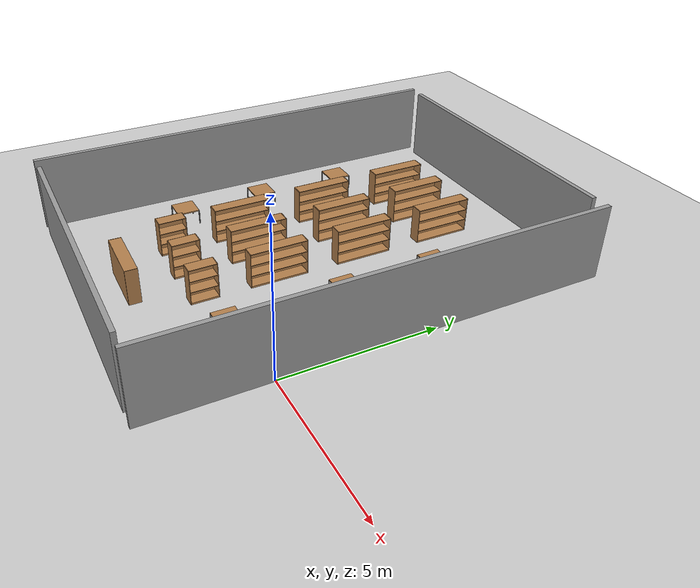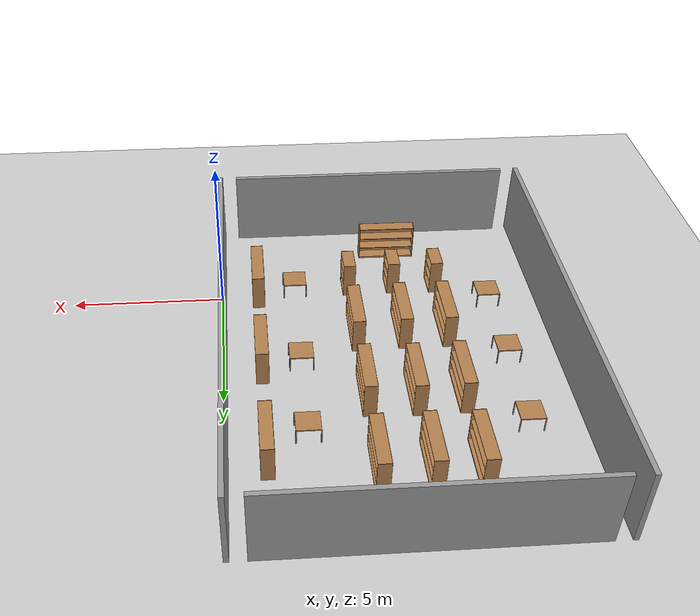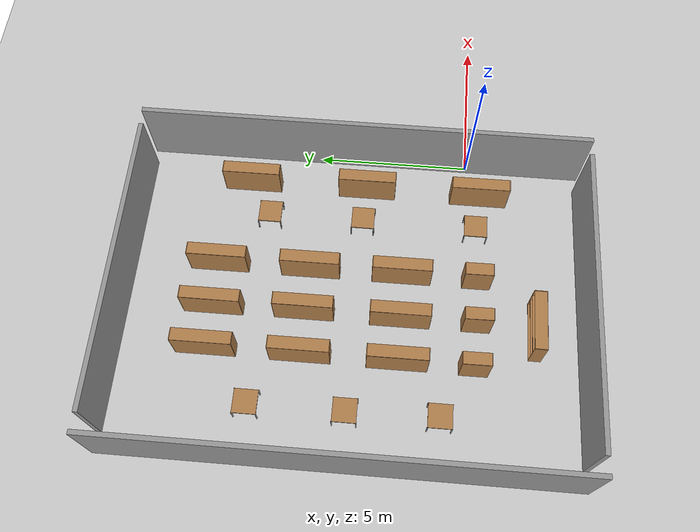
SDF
<sdf version="1.6">
 <world name="default">
  <light name="sun" type="directional">
   <pose>0 0 10 0 -0 0</pose>
   <diffuse>0.8 0.8 0.8 1</diffuse>
   <specular>0.2 0.2 0.2 1</specular>
   <attenuation>
    <range>1000</range>
    <constant>0.9</constant>
    <linear>0.01</linear>
    <quadratic>0.001</quadratic>
   </attenuation>
   <direction>-0.5 0.1 -0.9</direction>
   <spot><inner_angle>0</inner_angle><outer_angle>0</outer_angle><falloff>0</falloff></spot>
  </light>
  <model name="ground_plane">
   <static>1</static>
   <link name="link">
    <collision name="collision">
     <geometry><plane><normal>0 0 1</normal><size>100 100</size></plane></geometry>
     <surface><friction><ode><mu>100</mu><mu2>50</mu2></ode></friction></surface>
    </collision>
    <visual name="visual">
     <cast_shadows>0</cast_shadows>
     <geometry><plane><normal>0 0 1</normal><size>100 100</size></plane></geometry>
     <material>
      <script><uri>file://media/materials/scripts/gazebo.material</uri><name>Gazebo/Grey</name></script>
     </material>
    </visual>
   </link>
  </model>
  <gravity>0 0 -9.8</gravity>
  <magnetic_field>6e-06 2.3e-05 -4.2e-05</magnetic_field>
  <atmosphere type="adiabatic"/>
  <physics name="default_physics" default="0" type="ode">
   <max_step_size>0.001</max_step_size>
   <real_time_factor>1</real_time_factor>
   <real_time_update_rate>1000</real_time_update_rate>
  </physics>
  <scene><ambient>0.4 0.4 0.4 1</ambient><background>0.7 0.7 0.7 1</background><shadows>1</shadows></scene>
  <audio><device>default</device></audio>
  <spherical_coordinates>
   <surface_model>EARTH_WGS84</surface_model>
   <latitude_deg>0</latitude_deg>
   <longitude_deg>0</longitude_deg>
   <elevation>0</elevation>
   <heading_deg>0</heading_deg>
  </spherical_coordinates>
  <model name="bookshelf_1">
   <static>1</static>
   <link name="link">
    <inertial><mass>1</mass></inertial>
    <collision name="back">
     <pose>0 0.005 0.6 0 -0 0</pose>
     <geometry><box><size>0.9 0.01 1.2</size></box></geometry>
    </collision>
    <visual name="visual1">
     <pose>0 0.005 0.6 0 -0 0</pose>
     <geometry><box><size>0.9 0.01 1.2</size></box></geometry>
     <material>
      <script><uri>file://media/materials/scripts/gazebo.material</uri><name>Gazebo/Wood</name></script>
     </material>
    </visual>
    <collision name="left_side">
     <pose>0.45 -0.195 0.6 0 -0 0</pose>
     <geometry><box><size>0.02 0.4 1.2</size></box></geometry>
    </collision>
    <visual name="visual2">
     <pose>0.45 -0.195 0.6 0 -0 0</pose>
     <geometry><box><size>0.02 0.4 1.2</size></box></geometry>
     <material>
      <script><uri>file://media/materials/scripts/gazebo.material</uri><name>Gazebo/Wood</name></script>
     </material>
    </visual>
    <collision name="right_side">
     <pose>-0.45 -0.195 0.6 0 -0 0</pose>
     <geometry><box><size>0.02 0.4 1.2</size></box></geometry>
    </collision>
    <visual name="visual3">
     <pose>-0.45 -0.195 0.6 0 -0 0</pose>
     <geometry><box><size>0.02 0.4 1.2</size></box></geometry>
     <material>
      <script><uri>file://media/materials/scripts/gazebo.material</uri><name>Gazebo/Wood</name></script>
     </material>
    </visual>
    <collision name="bottom">
     <pose>0 -0.195 0.03 0 -0 0</pose>
     <geometry><box><size>0.88 0.4 0.06</size></box></geometry>
    </collision>
    <visual name="visual4">
     <pose>0 -0.195 0.03 0 -0 0</pose>
     <geometry><box><size>0.88 0.4 0.06</size></box></geometry>
     <material>
      <script><uri>file://media/materials/scripts/gazebo.material</uri><name>Gazebo/Wood</name></script>
     </material>
    </visual>
    <collision name="top">
     <pose>0 -0.195 1.19 0 -0 0</pose>
     <geometry><box><size>0.88 0.4 0.02</size></box></geometry>
    </collision>
    <visual name="visual5">
     <pose>0 -0.195 1.19 0 -0 0</pose>
     <geometry><box><size>0.88 0.4 0.02</size></box></geometry>
     <material>
      <script><uri>file://media/materials/scripts/gazebo.material</uri><name>Gazebo/Wood</name></script>
     </material>
    </visual>
    <collision name="low_shelf">
     <pose>0 -0.195 0.43 0 -0 0</pose>
     <geometry><box><size>0.88 0.4 0.02</size></box></geometry>
    </collision>
    <visual name="visual6">
     <pose>0 -0.195 0.43 0 -0 0</pose>
     <geometry><box><size>0.88 0.4 0.02</size></box></geometry>
     <material>
      <script><uri>file://media/materials/scripts/gazebo.material</uri><name>Gazebo/Wood</name></script>
     </material>
    </visual>
    <collision name="high_shelf">
     <pose>0 -0.195 0.8 0 -0 0</pose>
     <geometry><box><size>0.88 0.4 0.02</size></box></geometry>
    </collision>
    <visual name="visual7">
     <pose>0 -0.195 0.8 0 -0 0</pose>
     <geometry><box><size>0.88 0.4 0.02</size></box></geometry>
     <material>
      <script><uri>file://media/materials/scripts/gazebo.material</uri><name>Gazebo/Wood</name></script>
     </material>
    </visual>
   </link>
   <pose>-7.42871 -0.404892 0 0 -0 1.57898</pose>
  </model>
  <model name="bookshelf_2">
   <static>1</static>
   <link name="link">
    <inertial><mass>1</mass></inertial>
    <collision name="back">
     <pose>0 0.005 0.6 0 -0 0</pose>
     <geometry><box><size>0.9 0.01 1.2</size></box></geometry>
    </collision>
    <visual name="visual1">
     <pose>0 0.005 0.6 0 -0 0</pose>
     <geometry><box><size>0.9 0.01 1.2</size></box></geometry>
     <material>
      <script><uri>file://media/materials/scripts/gazebo.material</uri><name>Gazebo/Wood</name></script>
     </material>
    </visual>
    <collision name="left_side">
     <pose>0.45 -0.195 0.6 0 -0 0</pose>
     <geometry><box><size>0.02 0.4 1.2</size></box></geometry>
    </collision>
    <visual name="visual2">
     <pose>0.45 -0.195 0.6 0 -0 0</pose>
     <geometry><box><size>0.02 0.4 1.2</size></box></geometry>
     <material>
      <script><uri>file://media/materials/scripts/gazebo.material</uri><name>Gazebo/Wood</name></script>
     </material>
    </visual>
    <collision name="right_side">
     <pose>-0.45 -0.195 0.6 0 -0 0</pose>
     <geometry><box><size>0.02 0.4 1.2</size></box></geometry>
    </collision>
    <visual name="visual3">
     <pose>-0.45 -0.195 0.6 0 -0 0</pose>
     <geometry><box><size>0.02 0.4 1.2</size></box></geometry>
     <material>
      <script><uri>file://media/materials/scripts/gazebo.material</uri><name>Gazebo/Wood</name></script>
     </material>
    </visual>
    <collision name="bottom">
     <pose>0 -0.195 0.03 0 -0 0</pose>
     <geometry><box><size>0.88 0.4 0.06</size></box></geometry>
    </collision>
    <visual name="visual4">
     <pose>0 -0.195 0.03 0 -0 0</pose>
     <geometry><box><size>0.88 0.4 0.06</size></box></geometry>
     <material>
      <script><uri>file://media/materials/scripts/gazebo.material</uri><name>Gazebo/Wood</name></script>
     </material>
    </visual>
    <collision name="top">
     <pose>0 -0.195 1.19 0 -0 0</pose>
     <geometry><box><size>0.88 0.4 0.02</size></box></geometry>
    </collision>
    <visual name="visual5">
     <pose>0 -0.195 1.19 0 -0 0</pose>
     <geometry><box><size>0.88 0.4 0.02</size></box></geometry>
     <material>
      <script><uri>file://media/materials/scripts/gazebo.material</uri><name>Gazebo/Wood</name></script>
     </material>
    </visual>
    <collision name="low_shelf">
     <pose>0 -0.195 0.43 0 -0 0</pose>
     <geometry><box><size>0.88 0.4 0.02</size></box></geometry>
    </collision>
    <visual name="visual6">
     <pose>0 -0.195 0.43 0 -0 0</pose>
     <geometry><box><size>0.88 0.4 0.02</size></box></geometry>
     <material>
      <script><uri>file://media/materials/scripts/gazebo.material</uri><name>Gazebo/Wood</name></script>
     </material>
    </visual>
    <collision name="high_shelf">
     <pose>0 -0.195 0.8 0 -0 0</pose>
     <geometry><box><size>0.88 0.4 0.02</size></box></geometry>
    </collision>
    <visual name="visual7">
     <pose>0 -0.195 0.8 0 -0 0</pose>
     <geometry><box><size>0.88 0.4 0.02</size></box></geometry>
     <material>
      <script><uri>file://media/materials/scripts/gazebo.material</uri><name>Gazebo/Wood</name></script>
     </material>
    </visual>
   </link>
   <pose>-5.98331 -0.451994 0 0 -0 1.57898</pose>
  </model>
  <model name="bookshelf_3">
   <static>1</static>
   <link name="link">
    <inertial><mass>1</mass></inertial>
    <collision name="back">
     <pose>0 0.005 0.6 0 -0 0</pose>
     <geometry><box><size>0.9 0.01 1.2</size></box></geometry>
    </collision>
    <visual name="visual1">
     <pose>0 0.005 0.6 0 -0 0</pose>
     <geometry><box><size>0.9 0.01 1.2</size></box></geometry>
     <material>
      <script><uri>file://media/materials/scripts/gazebo.material</uri><name>Gazebo/Wood</name></script>
     </material>
    </visual>
    <collision name="left_side">
     <pose>0.45 -0.195 0.6 0 -0 0</pose>
     <geometry><box><size>0.02 0.4 1.2</size></box></geometry>
    </collision>
    <visual name="visual2">
     <pose>0.45 -0.195 0.6 0 -0 0</pose>
     <geometry><box><size>0.02 0.4 1.2</size></box></geometry>
     <material>
      <script><uri>file://media/materials/scripts/gazebo.material</uri><name>Gazebo/Wood</name></script>
     </material>
    </visual>
    <collision name="right_side">
     <pose>-0.45 -0.195 0.6 0 -0 0</pose>
     <geometry><box><size>0.02 0.4 1.2</size></box></geometry>
    </collision>
    <visual name="visual3">
     <pose>-0.45 -0.195 0.6 0 -0 0</pose>
     <geometry><box><size>0.02 0.4 1.2</size></box></geometry>
     <material>
      <script><uri>file://media/materials/scripts/gazebo.material</uri><name>Gazebo/Wood</name></script>
     </material>
    </visual>
    <collision name="bottom">
     <pose>0 -0.195 0.03 0 -0 0</pose>
     <geometry><box><size>0.88 0.4 0.06</size></box></geometry>
    </collision>
    <visual name="visual4">
     <pose>0 -0.195 0.03 0 -0 0</pose>
     <geometry><box><size>0.88 0.4 0.06</size></box></geometry>
     <material>
      <script><uri>file://media/materials/scripts/gazebo.material</uri><name>Gazebo/Wood</name></script>
     </material>
    </visual>
    <collision name="top">
     <pose>0 -0.195 1.19 0 -0 0</pose>
     <geometry><box><size>0.88 0.4 0.02</size></box></geometry>
    </collision>
    <visual name="visual5">
     <pose>0 -0.195 1.19 0 -0 0</pose>
     <geometry><box><size>0.88 0.4 0.02</size></box></geometry>
     <material>
      <script><uri>file://media/materials/scripts/gazebo.material</uri><name>Gazebo/Wood</name></script>
     </material>
    </visual>
    <collision name="low_shelf">
     <pose>0 -0.195 0.43 0 -0 0</pose>
     <geometry><box><size>0.88 0.4 0.02</size></box></geometry>
    </collision>
    <visual name="visual6">
     <pose>0 -0.195 0.43 0 -0 0</pose>
     <geometry><box><size>0.88 0.4 0.02</size></box></geometry>
     <material>
      <script><uri>file://media/materials/scripts/gazebo.material</uri><name>Gazebo/Wood</name></script>
     </material>
    </visual>
    <collision name="high_shelf">
     <pose>0 -0.195 0.8 0 -0 0</pose>
     <geometry><box><size>0.88 0.4 0.02</size></box></geometry>
    </collision>
    <visual name="visual7">
     <pose>0 -0.195 0.8 0 -0 0</pose>
     <geometry><box><size>0.88 0.4 0.02</size></box></geometry>
     <material>
      <script><uri>file://media/materials/scripts/gazebo.material</uri><name>Gazebo/Wood</name></script>
     </material>
    </visual>
   </link>
   <pose>-4.4879 -0.432889 0 0 -0 1.57898</pose>
  </model>
  <model name="bookshelf_4">
   <static>1</static>
   <link name="link">
    <inertial><mass>1</mass></inertial>
    <collision name="back">
     <pose>0 0.005 0.6 0 -0 0</pose>
     <geometry><box><size>1.9 0.01 1.2</size></box></geometry>
    </collision>
    <visual name="back">
     <pose>0 0.005 0.6 0 -0 0</pose>
     <geometry><box><size>1.9 0.01 1.2</size></box></geometry>
     <material>
      <script><uri>file://media/materials/scripts/gazebo.material</uri><name>Gazebo/Wood</name></script>
     </material>
    </visual>
    <collision name="left_side">
     <pose>0.95 -0.195 0.6 0 -0 0</pose>
     <geometry><box><size>0.02 0.4 1.2</size></box></geometry>
    </collision>
    <visual name="left_side">
     <pose>0.95 -0.195 0.6 0 -0 0</pose>
     <geometry><box><size>0.02 0.4 1.2</size></box></geometry>
     <material>
      <script><uri>file://media/materials/scripts/gazebo.material</uri><name>Gazebo/Wood</name></script>
     </material>
    </visual>
    <collision name="right_side">
     <pose>-0.95 -0.195 0.6 0 -0 0</pose>
     <geometry><box><size>0.02 0.4 1.2</size></box></geometry>
    </collision>
    <visual name="right_side">
     <pose>-0.95 -0.195 0.6 0 -0 0</pose>
     <geometry><box><size>0.02 0.4 1.2</size></box></geometry>
     <material>
      <script><uri>file://media/materials/scripts/gazebo.material</uri><name>Gazebo/Wood</name></script>
     </material>
    </visual>
    <collision name="bottom">
     <pose>0 -0.195 0.03 0 -0 0</pose>
     <geometry><box><size>1.88 0.4 0.06</size></box></geometry>
    </collision>
    <visual name="bottom">
     <pose>0 -0.195 0.03 0 -0 0</pose>
     <geometry><box><size>1.88 0.4 0.06</size></box></geometry>
     <material>
      <script><uri>file://media/materials/scripts/gazebo.material</uri><name>Gazebo/Wood</name></script>
     </material>
    </visual>
    <collision name="top">
     <pose>0 -0.195 1.19 0 -0 0</pose>
     <geometry><box><size>1.88 0.4 0.02</size></box></geometry>
    </collision>
    <visual name="top">
     <pose>0 -0.195 1.19 0 -0 0</pose>
     <geometry><box><size>1.88 0.4 0.02</size></box></geometry>
     <material>
      <script><uri>file://media/materials/scripts/gazebo.material</uri><name>Gazebo/Wood</name></script>
     </material>
    </visual>
    <collision name="low_shelf">
     <pose>0 -0.195 0.43 0 -0 0</pose>
     <geometry><box><size>1.88 0.4 0.02</size></box></geometry>
    </collision>
    <visual name="low_shelf">
     <pose>0 -0.195 0.43 0 -0 0</pose>
     <geometry><box><size>1.88 0.4 0.02</size></box></geometry>
     <material>
      <script><uri>file://media/materials/scripts/gazebo.material</uri><name>Gazebo/Wood</name></script>
     </material>
    </visual>
    <collision name="high_shelf">
     <pose>0 -0.195 0.8 0 -0 0</pose>
     <geometry><box><size>1.88 0.4 0.02</size></box></geometry>
    </collision>
    <visual name="high_shelf">
     <pose>0 -0.195 0.8 0 -0 0</pose>
     <geometry><box><size>1.88 0.4 0.02</size></box></geometry>
     <material>
      <script><uri>file://media/materials/scripts/gazebo.material</uri><name>Gazebo/Wood</name></script>
     </material>
    </visual>
   </link>
   <pose>-5.84093 -2.52343 0 0 -0 3.13337</pose>
  </model>
  <model name="table_1">
   <static>1</static>
   <link name="link">
    <collision name="surface">
     <pose>0 0 0.5 0 -0 0</pose>
     <geometry><box><size>0.75 0.75 0.04</size></box></geometry>
    </collision>
    <visual name="visual1">
     <pose>0 0 0.5 0 -0 0</pose>
     <geometry><box><size>0.75 0.75 0.04</size></box></geometry>
     <material>
      <script><uri>file://media/materials/scripts/gazebo.material</uri><name>Gazebo/Wood</name></script>
     </material>
    </visual>
    <collision name="front_left_leg">
     <pose>0.37 0.37 0.25 0 -0 0</pose>
     <geometry><cylinder><radius>0.02</radius><length>0.5</length></cylinder></geometry>
    </collision>
    <visual name="front_left_leg">
     <pose>0.37 0.37 0.25 0 -0 0</pose>
     <geometry><cylinder><radius>0.02</radius><length>0.5</length></cylinder></geometry>
     <material>
      <script><uri>file://media/materials/scripts/gazebo.material</uri><name>Gazebo/Grey</name></script>
     </material>
    </visual>
    <collision name="front_right_leg">
     <pose>0.37 -0.37 0.25 0 -0 0</pose>
     <geometry><cylinder><radius>0.02</radius><length>0.5</length></cylinder></geometry>
    </collision>
    <visual name="front_right_leg">
     <pose>0.37 -0.37 0.25 0 -0 0</pose>
     <geometry><cylinder><radius>0.02</radius><length>0.5</length></cylinder></geometry>
     <material>
      <script><uri>file://media/materials/scripts/gazebo.material</uri><name>Gazebo/Grey</name></script>
     </material>
    </visual>
    <collision name="back_right_leg">
     <pose>-0.37 -0.37 0.25 0 -0 0</pose>
     <geometry><cylinder><radius>0.02</radius><length>0.5</length></cylinder></geometry>
    </collision>
    <visual name="back_right_leg">
     <pose>-0.37 -0.37 0.25 0 -0 0</pose>
     <geometry><cylinder><radius>0.02</radius><length>0.5</length></cylinder></geometry>
     <material>
      <script><uri>file://media/materials/scripts/gazebo.material</uri><name>Gazebo/Grey</name></script>
     </material>
    </visual>
    <collision name="back_left_leg">
     <pose>-0.37 0.37 0.25 0 -0 0</pose>
     <geometry><cylinder><radius>0.02</radius><length>0.5</length></cylinder></geometry>
    </collision>
    <visual name="back_left_leg">
     <pose>-0.37 0.37 0.25 0 -0 0</pose>
     <geometry><cylinder><radius>0.02</radius><length>0.5</length></cylinder></geometry>
     <material>
      <script><uri>file://media/materials/scripts/gazebo.material</uri><name>Gazebo/Grey</name></script>
     </material>
    </visual>
    <velocity_decay><linear>0</linear><angular>0</angular></velocity_decay>
   </link>
   <pose>-2.45074 -0.350749 0 0 -0 0</pose>
  </model>
  <model name="table_2">
   <static>1</static>
   <link name="link">
    <collision name="surface">
     <pose>0 0 0.5 0 -0 0</pose>
     <geometry><box><size>0.75 0.75 0.04</size></box></geometry>
    </collision>
    <visual name="visual1">
     <pose>0 0 0.5 0 -0 0</pose>
     <geometry><box><size>0.75 0.75 0.04</size></box></geometry>
     <material>
      <script><uri>file://media/materials/scripts/gazebo.material</uri><name>Gazebo/Wood</name></script>
     </material>
    </visual>
    <collision name="front_left_leg">
     <pose>0.37 0.37 0.25 0 -0 0</pose>
     <geometry><cylinder><radius>0.02</radius><length>0.5</length></cylinder></geometry>
    </collision>
    <visual name="front_left_leg">
     <pose>0.37 0.37 0.25 0 -0 0</pose>
     <geometry><cylinder><radius>0.02</radius><length>0.5</length></cylinder></geometry>
     <material>
      <script><uri>file://media/materials/scripts/gazebo.material</uri><name>Gazebo/Grey</name></script>
     </material>
    </visual>
    <collision name="front_right_leg">
     <pose>0.37 -0.37 0.25 0 -0 0</pose>
     <geometry><cylinder><radius>0.02</radius><length>0.5</length></cylinder></geometry>
    </collision>
    <visual name="front_right_leg">
     <pose>0.37 -0.37 0.25 0 -0 0</pose>
     <geometry><cylinder><radius>0.02</radius><length>0.5</length></cylinder></geometry>
     <material>
      <script><uri>file://media/materials/scripts/gazebo.material</uri><name>Gazebo/Grey</name></script>
     </material>
    </visual>
    <collision name="back_right_leg">
     <pose>-0.37 -0.37 0.25 0 -0 0</pose>
     <geometry><cylinder><radius>0.02</radius><length>0.5</length></cylinder></geometry>
    </collision>
    <visual name="back_right_leg">
     <pose>-0.37 -0.37 0.25 0 -0 0</pose>
     <geometry><cylinder><radius>0.02</radius><length>0.5</length></cylinder></geometry>
     <material>
      <script><uri>file://media/materials/scripts/gazebo.material</uri><name>Gazebo/Grey</name></script>
     </material>
    </visual>
    <collision name="back_left_leg">
     <pose>-0.37 0.37 0.25 0 -0 0</pose>
     <geometry><cylinder><radius>0.02</radius><length>0.5</length></cylinder></geometry>
    </collision>
    <visual name="back_left_leg">
     <pose>-0.37 0.37 0.25 0 -0 0</pose>
     <geometry><cylinder><radius>0.02</radius><length>0.5</length></cylinder></geometry>
     <material>
      <script><uri>file://media/materials/scripts/gazebo.material</uri><name>Gazebo/Grey</name></script>
     </material>
    </visual>
    <velocity_decay><linear>0</linear><angular>0</angular></velocity_decay>
   </link>
   <pose>-2.43615 3.39841 0 0 -0 0</pose>
  </model>
  <model name="table_3">
   <static>1</static>
   <link name="link">
    <collision name="surface">
     <pose>0 0 0.5 0 -0 0</pose>
     <geometry><box><size>0.75 0.75 0.04</size></box></geometry>
    </collision>
    <visual name="visual1">
     <pose>0 0 0.5 0 -0 0</pose>
     <geometry><box><size>0.75 0.75 0.04</size></box></geometry>
     <material>
      <script><uri>file://media/materials/scripts/gazebo.material</uri><name>Gazebo/Wood</name></script>
     </material>
    </visual>
    <collision name="front_left_leg">
     <pose>0.37 0.37 0.25 0 -0 0</pose>
     <geometry><cylinder><radius>0.02</radius><length>0.5</length></cylinder></geometry>
    </collision>
    <visual name="front_left_leg">
     <pose>0.37 0.37 0.25 0 -0 0</pose>
     <geometry><cylinder><radius>0.02</radius><length>0.5</length></cylinder></geometry>
     <material>
      <script><uri>file://media/materials/scripts/gazebo.material</uri><name>Gazebo/Grey</name></script>
     </material>
    </visual>
    <collision name="front_right_leg">
     <pose>0.37 -0.37 0.25 0 -0 0</pose>
     <geometry><cylinder><radius>0.02</radius><length>0.5</length></cylinder></geometry>
    </collision>
    <visual name="front_right_leg">
     <pose>0.37 -0.37 0.25 0 -0 0</pose>
     <geometry><cylinder><radius>0.02</radius><length>0.5</length></cylinder></geometry>
     <material>
      <script><uri>file://media/materials/scripts/gazebo.material</uri><name>Gazebo/Grey</name></script>
     </material>
    </visual>
    <collision name="back_right_leg">
     <pose>-0.37 -0.37 0.25 0 -0 0</pose>
     <geometry><cylinder><radius>0.02</radius><length>0.5</length></cylinder></geometry>
    </collision>
    <visual name="back_right_leg">
     <pose>-0.37 -0.37 0.25 0 -0 0</pose>
     <geometry><cylinder><radius>0.02</radius><length>0.5</length></cylinder></geometry>
     <material>
      <script><uri>file://media/materials/scripts/gazebo.material</uri><name>Gazebo/Grey</name></script>
     </material>
    </visual>
    <collision name="back_left_leg">
     <pose>-0.37 0.37 0.25 0 -0 0</pose>
     <geometry><cylinder><radius>0.02</radius><length>0.5</length></cylinder></geometry>
    </collision>
    <visual name="back_left_leg">
     <pose>-0.37 0.37 0.25 0 -0 0</pose>
     <geometry><cylinder><radius>0.02</radius><length>0.5</length></cylinder></geometry>
     <material>
      <script><uri>file://media/materials/scripts/gazebo.material</uri><name>Gazebo/Grey</name></script>
     </material>
    </visual>
    <velocity_decay><linear>0</linear><angular>0</angular></velocity_decay>
   </link>
   <pose>-2.42969 6.50991 0 0 -0 0</pose>
  </model>
  <model name="table_4">
   <static>1</static>
   <link name="link">
    <collision name="surface">
     <pose>0 0 0.5 0 -0 0</pose>
     <geometry><box><size>0.75 0.75 0.04</size></box></geometry>
    </collision>
    <visual name="visual1">
     <pose>0 0 0.5 0 -0 0</pose>
     <geometry><box><size>0.75 0.75 0.04</size></box></geometry>
     <material>
      <script><uri>file://media/materials/scripts/gazebo.material</uri><name>Gazebo/Wood</name></script>
     </material>
    </visual>
    <collision name="front_left_leg">
     <pose>0.37 0.37 0.25 0 -0 0</pose>
     <geometry><cylinder><radius>0.02</radius><length>0.5</length></cylinder></geometry>
    </collision>
    <visual name="front_left_leg">
     <pose>0.37 0.37 0.25 0 -0 0</pose>
     <geometry><cylinder><radius>0.02</radius><length>0.5</length></cylinder></geometry>
     <material>
      <script><uri>file://media/materials/scripts/gazebo.material</uri><name>Gazebo/Grey</name></script>
     </material>
    </visual>
    <collision name="front_right_leg">
     <pose>0.37 -0.37 0.25 0 -0 0</pose>
     <geometry><cylinder><radius>0.02</radius><length>0.5</length></cylinder></geometry>
    </collision>
    <visual name="front_right_leg">
     <pose>0.37 -0.37 0.25 0 -0 0</pose>
     <geometry><cylinder><radius>0.02</radius><length>0.5</length></cylinder></geometry>
     <material>
      <script><uri>file://media/materials/scripts/gazebo.material</uri><name>Gazebo/Grey</name></script>
     </material>
    </visual>
    <collision name="back_right_leg">
     <pose>-0.37 -0.37 0.25 0 -0 0</pose>
     <geometry><cylinder><radius>0.02</radius><length>0.5</length></cylinder></geometry>
    </collision>
    <visual name="back_right_leg">
     <pose>-0.37 -0.37 0.25 0 -0 0</pose>
     <geometry><cylinder><radius>0.02</radius><length>0.5</length></cylinder></geometry>
     <material>
      <script><uri>file://media/materials/scripts/gazebo.material</uri><name>Gazebo/Grey</name></script>
     </material>
    </visual>
    <collision name="back_left_leg">
     <pose>-0.37 0.37 0.25 0 -0 0</pose>
     <geometry><cylinder><radius>0.02</radius><length>0.5</length></cylinder></geometry>
    </collision>
    <visual name="back_left_leg">
     <pose>-0.37 0.37 0.25 0 -0 0</pose>
     <geometry><cylinder><radius>0.02</radius><length>0.5</length></cylinder></geometry>
     <material>
      <script><uri>file://media/materials/scripts/gazebo.material</uri><name>Gazebo/Grey</name></script>
     </material>
    </visual>
    <velocity_decay><linear>0</linear><angular>0</angular></velocity_decay>
   </link>
   <pose>-8.88942 0.594744 0 0 -0 0</pose>
  </model>
  <model name="table_5">
   <static>1</static>
   <link name="link">
    <collision name="surface">
     <pose>0 0 0.5 0 -0 0</pose>
     <geometry><box><size>0.75 0.75 0.04</size></box></geometry>
    </collision>
    <visual name="visual1">
     <pose>0 0 0.5 0 -0 0</pose>
     <geometry><box><size>0.75 0.75 0.04</size></box></geometry>
     <material>
      <script><uri>file://media/materials/scripts/gazebo.material</uri><name>Gazebo/Wood</name></script>
     </material>
    </visual>
    <collision name="front_left_leg">
     <pose>0.37 0.37 0.25 0 -0 0</pose>
     <geometry><cylinder><radius>0.02</radius><length>0.5</length></cylinder></geometry>
    </collision>
    <visual name="front_left_leg">
     <pose>0.37 0.37 0.25 0 -0 0</pose>
     <geometry><cylinder><radius>0.02</radius><length>0.5</length></cylinder></geometry>
     <material>
      <script><uri>file://media/materials/scripts/gazebo.material</uri><name>Gazebo/Grey</name></script>
     </material>
    </visual>
    <collision name="front_right_leg">
     <pose>0.37 -0.37 0.25 0 -0 0</pose>
     <geometry><cylinder><radius>0.02</radius><length>0.5</length></cylinder></geometry>
    </collision>
    <visual name="front_right_leg">
     <pose>0.37 -0.37 0.25 0 -0 0</pose>
     <geometry><cylinder><radius>0.02</radius><length>0.5</length></cylinder></geometry>
     <material>
      <script><uri>file://media/materials/scripts/gazebo.material</uri><name>Gazebo/Grey</name></script>
     </material>
    </visual>
    <collision name="back_right_leg">
     <pose>-0.37 -0.37 0.25 0 -0 0</pose>
     <geometry><cylinder><radius>0.02</radius><length>0.5</length></cylinder></geometry>
    </collision>
    <visual name="back_right_leg">
     <pose>-0.37 -0.37 0.25 0 -0 0</pose>
     <geometry><cylinder><radius>0.02</radius><length>0.5</length></cylinder></geometry>
     <material>
      <script><uri>file://media/materials/scripts/gazebo.material</uri><name>Gazebo/Grey</name></script>
     </material>
    </visual>
    <collision name="back_left_leg">
     <pose>-0.37 0.37 0.25 0 -0 0</pose>
     <geometry><cylinder><radius>0.02</radius><length>0.5</length></cylinder></geometry>
    </collision>
    <visual name="back_left_leg">
     <pose>-0.37 0.37 0.25 0 -0 0</pose>
     <geometry><cylinder><radius>0.02</radius><length>0.5</length></cylinder></geometry>
     <material>
      <script><uri>file://media/materials/scripts/gazebo.material</uri><name>Gazebo/Grey</name></script>
     </material>
    </visual>
    <velocity_decay><linear>0</linear><angular>0</angular></velocity_decay>
   </link>
   <pose>-8.9429 3.46794 0 0 -0 0</pose>
  </model>
  <model name="table_6">
   <static>1</static>
   <link name="link">
    <collision name="surface">
     <pose>0 0 0.5 0 -0 0</pose>
     <geometry><box><size>0.75 0.75 0.04</size></box></geometry>
    </collision>
    <visual name="visual1">
     <pose>0 0 0.5 0 -0 0</pose>
     <geometry><box><size>0.75 0.75 0.04</size></box></geometry>
     <material>
      <script><uri>file://media/materials/scripts/gazebo.material</uri><name>Gazebo/Wood</name></script>
     </material>
    </visual>
    <collision name="front_left_leg">
     <pose>0.37 0.37 0.25 0 -0 0</pose>
     <geometry><cylinder><radius>0.02</radius><length>0.5</length></cylinder></geometry>
    </collision>
    <visual name="front_left_leg">
     <pose>0.37 0.37 0.25 0 -0 0</pose>
     <geometry><cylinder><radius>0.02</radius><length>0.5</length></cylinder></geometry>
     <material>
      <script><uri>file://media/materials/scripts/gazebo.material</uri><name>Gazebo/Grey</name></script>
     </material>
    </visual>
    <collision name="front_right_leg">
     <pose>0.37 -0.37 0.25 0 -0 0</pose>
     <geometry><cylinder><radius>0.02</radius><length>0.5</length></cylinder></geometry>
    </collision>
    <visual name="front_right_leg">
     <pose>0.37 -0.37 0.25 0 -0 0</pose>
     <geometry><cylinder><radius>0.02</radius><length>0.5</length></cylinder></geometry>
     <material>
      <script><uri>file://media/materials/scripts/gazebo.material</uri><name>Gazebo/Grey</name></script>
     </material>
    </visual>
    <collision name="back_right_leg">
     <pose>-0.37 -0.37 0.25 0 -0 0</pose>
     <geometry><cylinder><radius>0.02</radius><length>0.5</length></cylinder></geometry>
    </collision>
    <visual name="back_right_leg">
     <pose>-0.37 -0.37 0.25 0 -0 0</pose>
     <geometry><cylinder><radius>0.02</radius><length>0.5</length></cylinder></geometry>
     <material>
      <script><uri>file://media/materials/scripts/gazebo.material</uri><name>Gazebo/Grey</name></script>
     </material>
    </visual>
    <collision name="back_left_leg">
     <pose>-0.37 0.37 0.25 0 -0 0</pose>
     <geometry><cylinder><radius>0.02</radius><length>0.5</length></cylinder></geometry>
    </collision>
    <visual name="back_left_leg">
     <pose>-0.37 0.37 0.25 0 -0 0</pose>
     <geometry><cylinder><radius>0.02</radius><length>0.5</length></cylinder></geometry>
     <material>
      <script><uri>file://media/materials/scripts/gazebo.material</uri><name>Gazebo/Grey</name></script>
     </material>
    </visual>
    <velocity_decay><linear>0</linear><angular>0</angular></velocity_decay>
   </link>
   <pose>-8.9174 6.48694 0 0 -0 0</pose>
  </model>
  <model name="walls">
   <pose>-5.34 3.52 0 0 -0 0</pose>
   <link name="wall_1">
    <collision name="wall_1_Collision">
     <geometry><box><size>9.5 0.15 2.5</size></box></geometry>
     <pose>0 0 1.25 0 -0 0</pose>
    </collision>
    <visual name="wall_1_Visual">
     <pose>0 0 1.25 0 -0 0</pose>
     <geometry><box><size>9.5 0.15 2.5</size></box></geometry>
     <material>
      <script><uri>file://media/materials/scripts/gazebo.material</uri><name>Gazebo/Grey</name></script>
      <ambient>1 1 1 1</ambient>
     </material>
     <meta><layer>0</layer></meta>
    </visual>
    <pose>0 -7.3 0 0 -0 0</pose>
   </link>
   <link name="wall_2">
    <collision name="wall_2_Collision">
     <geometry><box><size>14.75 0.15 2.5</size></box></geometry>
     <pose>0 0 1.25 0 -0 0</pose>
    </collision>
    <visual name="wall_2_Visual">
     <pose>0 0 1.25 0 -0 0</pose>
     <geometry><box><size>14.75 0.15 2.5</size></box></geometry>
     <material>
      <script><uri>file://media/materials/scripts/gazebo.material</uri><name>Gazebo/Grey</name></script>
      <ambient>1 1 1 1</ambient>
     </material>
     <meta><layer>0</layer></meta>
    </visual>
    <pose>5.3 0 0 0 -0 1.5708</pose>
   </link>
   <link name="wall_3">
    <collision name="wall_3_Collision">
     <geometry><box><size>9.5 0.15 2.5</size></box></geometry>
     <pose>0 0 1.25 0 -0 0</pose>
    </collision>
    <visual name="wall_3_Visual">
     <pose>0 0 1.25 0 -0 0</pose>
     <geometry><box><size>9.5 0.15 2.5</size></box></geometry>
     <material>
      <script><uri>file://media/materials/scripts/gazebo.material</uri><name>Gazebo/Grey</name></script>
      <ambient>1 1 1 1</ambient>
     </material>
     <meta><layer>0</layer></meta>
    </visual>
    <pose>0 7.3 0 0 -0 3.14159</pose>
   </link>
   <link name="wall_4">
    <collision name="wall_4_Collision">
     <geometry><box><size>14.75 0.15 2.5</size></box></geometry>
     <pose>0 0 1.25 0 -0 0</pose>
    </collision>
    <visual name="wall_4_Visual">
     <pose>0 0 1.25 0 -0 0</pose>
     <geometry><box><size>14.75 0.15 2.5</size></box></geometry>
     <material>
      <script><uri>file://media/materials/scripts/gazebo.material</uri><name>Gazebo/Grey</name></script>
      <ambient>1 1 1 1</ambient>
     </material>
     <meta><layer>0</layer></meta>
    </visual>
    <pose>-5.3 0 0 0 -0 -1.5708</pose>
   </link>
   <static>1</static>
  </model>
  <model name="bookshelf_5">
   <static>1</static>
   <link name="link">
    <inertial><mass>1</mass></inertial>
    <collision name="back">
     <pose>0 0.005 0.6 0 -0 0</pose>
     <geometry><box><size>1.9 0.01 1.2</size></box></geometry>
    </collision>
    <visual name="back">
     <pose>0 0.005 0.6 0 -0 0</pose>
     <geometry><box><size>1.9 0.01 1.2</size></box></geometry>
     <material>
      <script><uri>file://media/materials/scripts/gazebo.material</uri><name>Gazebo/Wood</name></script>
     </material>
    </visual>
    <collision name="left_side">
     <pose>0.95 -0.195 0.6 0 -0 0</pose>
     <geometry><box><size>0.02 0.4 1.2</size></box></geometry>
    </collision>
    <visual name="left_side">
     <pose>0.95 -0.195 0.6 0 -0 0</pose>
     <geometry><box><size>0.02 0.4 1.2</size></box></geometry>
     <material>
      <script><uri>file://media/materials/scripts/gazebo.material</uri><name>Gazebo/Wood</name></script>
     </material>
    </visual>
    <collision name="right_side">
     <pose>-0.95 -0.195 0.6 0 -0 0</pose>
     <geometry><box><size>0.02 0.4 1.2</size></box></geometry>
    </collision>
    <visual name="right_side">
     <pose>-0.95 -0.195 0.6 0 -0 0</pose>
     <geometry><box><size>0.02 0.4 1.2</size></box></geometry>
     <material>
      <script><uri>file://media/materials/scripts/gazebo.material</uri><name>Gazebo/Wood</name></script>
     </material>
    </visual>
    <collision name="bottom">
     <pose>0 -0.195 0.03 0 -0 0</pose>
     <geometry><box><size>1.88 0.4 0.06</size></box></geometry>
    </collision>
    <visual name="bottom">
     <pose>0 -0.195 0.03 0 -0 0</pose>
     <geometry><box><size>1.88 0.4 0.06</size></box></geometry>
     <material>
      <script><uri>file://media/materials/scripts/gazebo.material</uri><name>Gazebo/Wood</name></script>
     </material>
    </visual>
    <collision name="top">
     <pose>0 -0.195 1.19 0 -0 0</pose>
     <geometry><box><size>1.88 0.4 0.02</size></box></geometry>
    </collision>
    <visual name="top">
     <pose>0 -0.195 1.19 0 -0 0</pose>
     <geometry><box><size>1.88 0.4 0.02</size></box></geometry>
     <material>
      <script><uri>file://media/materials/scripts/gazebo.material</uri><name>Gazebo/Wood</name></script>
     </material>
    </visual>
    <collision name="low_shelf">
     <pose>0 -0.195 0.43 0 -0 0</pose>
     <geometry><box><size>1.88 0.4 0.02</size></box></geometry>
    </collision>
    <visual name="low_shelf">
     <pose>0 -0.195 0.43 0 -0 0</pose>
     <geometry><box><size>1.88 0.4 0.02</size></box></geometry>
     <material>
      <script><uri>file://media/materials/scripts/gazebo.material</uri><name>Gazebo/Wood</name></script>
     </material>
    </visual>
    <collision name="high_shelf">
     <pose>0 -0.195 0.8 0 -0 0</pose>
     <geometry><box><size>1.88 0.4 0.02</size></box></geometry>
    </collision>
    <visual name="high_shelf">
     <pose>0 -0.195 0.8 0 -0 0</pose>
     <geometry><box><size>1.88 0.4 0.02</size></box></geometry>
     <material>
      <script><uri>file://media/materials/scripts/gazebo.material</uri><name>Gazebo/Wood</name></script>
     </material>
    </visual>
   </link>
   <pose>-4.49483 4.97096 0 0 0.002317 1.57295</pose>
  </model>
  <model name="bookshelf_6">
   <static>1</static>
   <link name="link">
    <inertial><mass>1</mass></inertial>
    <collision name="back">
     <pose>0 0.005 0.6 0 -0 0</pose>
     <geometry><box><size>1.9 0.01 1.2</size></box></geometry>
    </collision>
    <visual name="back">
     <pose>0 0.005 0.6 0 -0 0</pose>
     <geometry><box><size>1.9 0.01 1.2</size></box></geometry>
     <material>
      <script><uri>file://media/materials/scripts/gazebo.material</uri><name>Gazebo/Wood</name></script>
     </material>
    </visual>
    <collision name="left_side">
     <pose>0.95 -0.195 0.6 0 -0 0</pose>
     <geometry><box><size>0.02 0.4 1.2</size></box></geometry>
    </collision>
    <visual name="left_side">
     <pose>0.95 -0.195 0.6 0 -0 0</pose>
     <geometry><box><size>0.02 0.4 1.2</size></box></geometry>
     <material>
      <script><uri>file://media/materials/scripts/gazebo.material</uri><name>Gazebo/Wood</name></script>
     </material>
    </visual>
    <collision name="right_side">
     <pose>-0.95 -0.195 0.6 0 -0 0</pose>
     <geometry><box><size>0.02 0.4 1.2</size></box></geometry>
    </collision>
    <visual name="right_side">
     <pose>-0.95 -0.195 0.6 0 -0 0</pose>
     <geometry><box><size>0.02 0.4 1.2</size></box></geometry>
     <material>
      <script><uri>file://media/materials/scripts/gazebo.material</uri><name>Gazebo/Wood</name></script>
     </material>
    </visual>
    <collision name="bottom">
     <pose>0 -0.195 0.03 0 -0 0</pose>
     <geometry><box><size>1.88 0.4 0.06</size></box></geometry>
    </collision>
    <visual name="bottom">
     <pose>0 -0.195 0.03 0 -0 0</pose>
     <geometry><box><size>1.88 0.4 0.06</size></box></geometry>
     <material>
      <script><uri>file://media/materials/scripts/gazebo.material</uri><name>Gazebo/Wood</name></script>
     </material>
    </visual>
    <collision name="top">
     <pose>0 -0.195 1.19 0 -0 0</pose>
     <geometry><box><size>1.88 0.4 0.02</size></box></geometry>
    </collision>
    <visual name="top">
     <pose>0 -0.195 1.19 0 -0 0</pose>
     <geometry><box><size>1.88 0.4 0.02</size></box></geometry>
     <material>
      <script><uri>file://media/materials/scripts/gazebo.material</uri><name>Gazebo/Wood</name></script>
     </material>
    </visual>
    <collision name="low_shelf">
     <pose>0 -0.195 0.43 0 -0 0</pose>
     <geometry><box><size>1.88 0.4 0.02</size></box></geometry>
    </collision>
    <visual name="low_shelf">
     <pose>0 -0.195 0.43 0 -0 0</pose>
     <geometry><box><size>1.88 0.4 0.02</size></box></geometry>
     <material>
      <script><uri>file://media/materials/scripts/gazebo.material</uri><name>Gazebo/Wood</name></script>
     </material>
    </visual>
    <collision name="high_shelf">
     <pose>0 -0.195 0.8 0 -0 0</pose>
     <geometry><box><size>1.88 0.4 0.02</size></box></geometry>
    </collision>
    <visual name="high_shelf">
     <pose>0 -0.195 0.8 0 -0 0</pose>
     <geometry><box><size>1.88 0.4 0.02</size></box></geometry>
     <material>
      <script><uri>file://media/materials/scripts/gazebo.material</uri><name>Gazebo/Wood</name></script>
     </material>
    </visual>
   </link>
   <pose>-4.48812 2.00352 0 0 0.002317 1.57295</pose>
  </model>
  <model name="bookshelf_7">
   <static>1</static>
   <link name="link">
    <inertial><mass>1</mass></inertial>
    <collision name="back">
     <pose>0 0.005 0.6 0 -0 0</pose>
     <geometry><box><size>1.9 0.01 1.2</size></box></geometry>
    </collision>
    <visual name="back">
     <pose>0 0.005 0.6 0 -0 0</pose>
     <geometry><box><size>1.9 0.01 1.2</size></box></geometry>
     <material>
      <script><uri>file://media/materials/scripts/gazebo.material</uri><name>Gazebo/Wood</name></script>
     </material>
    </visual>
    <collision name="left_side">
     <pose>0.95 -0.195 0.6 0 -0 0</pose>
     <geometry><box><size>0.02 0.4 1.2</size></box></geometry>
    </collision>
    <visual name="left_side">
     <pose>0.95 -0.195 0.6 0 -0 0</pose>
     <geometry><box><size>0.02 0.4 1.2</size></box></geometry>
     <material>
      <script><uri>file://media/materials/scripts/gazebo.material</uri><name>Gazebo/Wood</name></script>
     </material>
    </visual>
    <collision name="right_side">
     <pose>-0.95 -0.195 0.6 0 -0 0</pose>
     <geometry><box><size>0.02 0.4 1.2</size></box></geometry>
    </collision>
    <visual name="right_side">
     <pose>-0.95 -0.195 0.6 0 -0 0</pose>
     <geometry><box><size>0.02 0.4 1.2</size></box></geometry>
     <material>
      <script><uri>file://media/materials/scripts/gazebo.material</uri><name>Gazebo/Wood</name></script>
     </material>
    </visual>
    <collision name="bottom">
     <pose>0 -0.195 0.03 0 -0 0</pose>
     <geometry><box><size>1.88 0.4 0.06</size></box></geometry>
    </collision>
    <visual name="bottom">
     <pose>0 -0.195 0.03 0 -0 0</pose>
     <geometry><box><size>1.88 0.4 0.06</size></box></geometry>
     <material>
      <script><uri>file://media/materials/scripts/gazebo.material</uri><name>Gazebo/Wood</name></script>
     </material>
    </visual>
    <collision name="top">
     <pose>0 -0.195 1.19 0 -0 0</pose>
     <geometry><box><size>1.88 0.4 0.02</size></box></geometry>
    </collision>
    <visual name="top">
     <pose>0 -0.195 1.19 0 -0 0</pose>
     <geometry><box><size>1.88 0.4 0.02</size></box></geometry>
     <material>
      <script><uri>file://media/materials/scripts/gazebo.material</uri><name>Gazebo/Wood</name></script>
     </material>
    </visual>
    <collision name="low_shelf">
     <pose>0 -0.195 0.43 0 -0 0</pose>
     <geometry><box><size>1.88 0.4 0.02</size></box></geometry>
    </collision>
    <visual name="low_shelf">
     <pose>0 -0.195 0.43 0 -0 0</pose>
     <geometry><box><size>1.88 0.4 0.02</size></box></geometry>
     <material>
      <script><uri>file://media/materials/scripts/gazebo.material</uri><name>Gazebo/Wood</name></script>
     </material>
    </visual>
    <collision name="high_shelf">
     <pose>0 -0.195 0.8 0 -0 0</pose>
     <geometry><box><size>1.88 0.4 0.02</size></box></geometry>
    </collision>
    <visual name="high_shelf">
     <pose>0 -0.195 0.8 0 -0 0</pose>
     <geometry><box><size>1.88 0.4 0.02</size></box></geometry>
     <material>
      <script><uri>file://media/materials/scripts/gazebo.material</uri><name>Gazebo/Wood</name></script>
     </material>
    </visual>
   </link>
   <pose>-4.49264 7.96878 0 0 0.002317 1.57295</pose>
  </model>
  <model name="bookshelf_8">
   <static>1</static>
   <link name="link">
    <inertial><mass>1</mass></inertial>
    <collision name="back">
     <pose>0 0.005 0.6 0 -0 0</pose>
     <geometry><box><size>1.9 0.01 1.2</size></box></geometry>
    </collision>
    <visual name="back">
     <pose>0 0.005 0.6 0 -0 0</pose>
     <geometry><box><size>1.9 0.01 1.2</size></box></geometry>
     <material>
      <script><uri>file://media/materials/scripts/gazebo.material</uri><name>Gazebo/Wood</name></script>
     </material>
    </visual>
    <collision name="left_side">
     <pose>0.95 -0.195 0.6 0 -0 0</pose>
     <geometry><box><size>0.02 0.4 1.2</size></box></geometry>
    </collision>
    <visual name="left_side">
     <pose>0.95 -0.195 0.6 0 -0 0</pose>
     <geometry><box><size>0.02 0.4 1.2</size></box></geometry>
     <material>
      <script><uri>file://media/materials/scripts/gazebo.material</uri><name>Gazebo/Wood</name></script>
     </material>
    </visual>
    <collision name="right_side">
     <pose>-0.95 -0.195 0.6 0 -0 0</pose>
     <geometry><box><size>0.02 0.4 1.2</size></box></geometry>
    </collision>
    <visual name="right_side">
     <pose>-0.95 -0.195 0.6 0 -0 0</pose>
     <geometry><box><size>0.02 0.4 1.2</size></box></geometry>
     <material>
      <script><uri>file://media/materials/scripts/gazebo.material</uri><name>Gazebo/Wood</name></script>
     </material>
    </visual>
    <collision name="bottom">
     <pose>0 -0.195 0.03 0 -0 0</pose>
     <geometry><box><size>1.88 0.4 0.06</size></box></geometry>
    </collision>
    <visual name="bottom">
     <pose>0 -0.195 0.03 0 -0 0</pose>
     <geometry><box><size>1.88 0.4 0.06</size></box></geometry>
     <material>
      <script><uri>file://media/materials/scripts/gazebo.material</uri><name>Gazebo/Wood</name></script>
     </material>
    </visual>
    <collision name="top">
     <pose>0 -0.195 1.19 0 -0 0</pose>
     <geometry><box><size>1.88 0.4 0.02</size></box></geometry>
    </collision>
    <visual name="top">
     <pose>0 -0.195 1.19 0 -0 0</pose>
     <geometry><box><size>1.88 0.4 0.02</size></box></geometry>
     <material>
      <script><uri>file://media/materials/scripts/gazebo.material</uri><name>Gazebo/Wood</name></script>
     </material>
    </visual>
    <collision name="low_shelf">
     <pose>0 -0.195 0.43 0 -0 0</pose>
     <geometry><box><size>1.88 0.4 0.02</size></box></geometry>
    </collision>
    <visual name="low_shelf">
     <pose>0 -0.195 0.43 0 -0 0</pose>
     <geometry><box><size>1.88 0.4 0.02</size></box></geometry>
     <material>
      <script><uri>file://media/materials/scripts/gazebo.material</uri><name>Gazebo/Wood</name></script>
     </material>
    </visual>
    <collision name="high_shelf">
     <pose>0 -0.195 0.8 0 -0 0</pose>
     <geometry><box><size>1.88 0.4 0.02</size></box></geometry>
    </collision>
    <visual name="high_shelf">
     <pose>0 -0.195 0.8 0 -0 0</pose>
     <geometry><box><size>1.88 0.4 0.02</size></box></geometry>
     <material>
      <script><uri>file://media/materials/scripts/gazebo.material</uri><name>Gazebo/Wood</name></script>
     </material>
    </visual>
   </link>
   <pose>-6.00199 7.96031 0 0 0.002317 1.57295</pose>
  </model>
  <model name="bookshelf_9">
   <static>1</static>
   <link name="link">
    <inertial><mass>1</mass></inertial>
    <collision name="back">
     <pose>0 0.005 0.6 0 -0 0</pose>
     <geometry><box><size>1.9 0.01 1.2</size></box></geometry>
    </collision>
    <visual name="back">
     <pose>0 0.005 0.6 0 -0 0</pose>
     <geometry><box><size>1.9 0.01 1.2</size></box></geometry>
     <material>
      <script><uri>file://media/materials/scripts/gazebo.material</uri><name>Gazebo/Wood</name></script>
     </material>
    </visual>
    <collision name="left_side">
     <pose>0.95 -0.195 0.6 0 -0 0</pose>
     <geometry><box><size>0.02 0.4 1.2</size></box></geometry>
    </collision>
    <visual name="left_side">
     <pose>0.95 -0.195 0.6 0 -0 0</pose>
     <geometry><box><size>0.02 0.4 1.2</size></box></geometry>
     <material>
      <script><uri>file://media/materials/scripts/gazebo.material</uri><name>Gazebo/Wood</name></script>
     </material>
    </visual>
    <collision name="right_side">
     <pose>-0.95 -0.195 0.6 0 -0 0</pose>
     <geometry><box><size>0.02 0.4 1.2</size></box></geometry>
    </collision>
    <visual name="right_side">
     <pose>-0.95 -0.195 0.6 0 -0 0</pose>
     <geometry><box><size>0.02 0.4 1.2</size></box></geometry>
     <material>
      <script><uri>file://media/materials/scripts/gazebo.material</uri><name>Gazebo/Wood</name></script>
     </material>
    </visual>
    <collision name="bottom">
     <pose>0 -0.195 0.03 0 -0 0</pose>
     <geometry><box><size>1.88 0.4 0.06</size></box></geometry>
    </collision>
    <visual name="bottom">
     <pose>0 -0.195 0.03 0 -0 0</pose>
     <geometry><box><size>1.88 0.4 0.06</size></box></geometry>
     <material>
      <script><uri>file://media/materials/scripts/gazebo.material</uri><name>Gazebo/Wood</name></script>
     </material>
    </visual>
    <collision name="top">
     <pose>0 -0.195 1.19 0 -0 0</pose>
     <geometry><box><size>1.88 0.4 0.02</size></box></geometry>
    </collision>
    <visual name="top">
     <pose>0 -0.195 1.19 0 -0 0</pose>
     <geometry><box><size>1.88 0.4 0.02</size></box></geometry>
     <material>
      <script><uri>file://media/materials/scripts/gazebo.material</uri><name>Gazebo/Wood</name></script>
     </material>
    </visual>
    <collision name="low_shelf">
     <pose>0 -0.195 0.43 0 -0 0</pose>
     <geometry><box><size>1.88 0.4 0.02</size></box></geometry>
    </collision>
    <visual name="low_shelf">
     <pose>0 -0.195 0.43 0 -0 0</pose>
     <geometry><box><size>1.88 0.4 0.02</size></box></geometry>
     <material>
      <script><uri>file://media/materials/scripts/gazebo.material</uri><name>Gazebo/Wood</name></script>
     </material>
    </visual>
    <collision name="high_shelf">
     <pose>0 -0.195 0.8 0 -0 0</pose>
     <geometry><box><size>1.88 0.4 0.02</size></box></geometry>
    </collision>
    <visual name="high_shelf">
     <pose>0 -0.195 0.8 0 -0 0</pose>
     <geometry><box><size>1.88 0.4 0.02</size></box></geometry>
     <material>
      <script><uri>file://media/materials/scripts/gazebo.material</uri><name>Gazebo/Wood</name></script>
     </material>
    </visual>
   </link>
   <pose>-5.97352 5.03693 0 0 0.002317 1.57295</pose>
  </model>
  <model name="bookshelf_10">
   <static>1</static>
   <link name="link">
    <inertial><mass>1</mass></inertial>
    <collision name="back">
     <pose>0 0.005 0.6 0 -0 0</pose>
     <geometry><box><size>1.9 0.01 1.2</size></box></geometry>
    </collision>
    <visual name="back">
     <pose>0 0.005 0.6 0 -0 0</pose>
     <geometry><box><size>1.9 0.01 1.2</size></box></geometry>
     <material>
      <script><uri>file://media/materials/scripts/gazebo.material</uri><name>Gazebo/Wood</name></script>
     </material>
    </visual>
    <collision name="left_side">
     <pose>0.95 -0.195 0.6 0 -0 0</pose>
     <geometry><box><size>0.02 0.4 1.2</size></box></geometry>
    </collision>
    <visual name="left_side">
     <pose>0.95 -0.195 0.6 0 -0 0</pose>
     <geometry><box><size>0.02 0.4 1.2</size></box></geometry>
     <material>
      <script><uri>file://media/materials/scripts/gazebo.material</uri><name>Gazebo/Wood</name></script>
     </material>
    </visual>
    <collision name="right_side">
     <pose>-0.95 -0.195 0.6 0 -0 0</pose>
     <geometry><box><size>0.02 0.4 1.2</size></box></geometry>
    </collision>
    <visual name="right_side">
     <pose>-0.95 -0.195 0.6 0 -0 0</pose>
     <geometry><box><size>0.02 0.4 1.2</size></box></geometry>
     <material>
      <script><uri>file://media/materials/scripts/gazebo.material</uri><name>Gazebo/Wood</name></script>
     </material>
    </visual>
    <collision name="bottom">
     <pose>0 -0.195 0.03 0 -0 0</pose>
     <geometry><box><size>1.88 0.4 0.06</size></box></geometry>
    </collision>
    <visual name="bottom">
     <pose>0 -0.195 0.03 0 -0 0</pose>
     <geometry><box><size>1.88 0.4 0.06</size></box></geometry>
     <material>
      <script><uri>file://media/materials/scripts/gazebo.material</uri><name>Gazebo/Wood</name></script>
     </material>
    </visual>
    <collision name="top">
     <pose>0 -0.195 1.19 0 -0 0</pose>
     <geometry><box><size>1.88 0.4 0.02</size></box></geometry>
    </collision>
    <visual name="top">
     <pose>0 -0.195 1.19 0 -0 0</pose>
     <geometry><box><size>1.88 0.4 0.02</size></box></geometry>
     <material>
      <script><uri>file://media/materials/scripts/gazebo.material</uri><name>Gazebo/Wood</name></script>
     </material>
    </visual>
    <collision name="low_shelf">
     <pose>0 -0.195 0.43 0 -0 0</pose>
     <geometry><box><size>1.88 0.4 0.02</size></box></geometry>
    </collision>
    <visual name="low_shelf">
     <pose>0 -0.195 0.43 0 -0 0</pose>
     <geometry><box><size>1.88 0.4 0.02</size></box></geometry>
     <material>
      <script><uri>file://media/materials/scripts/gazebo.material</uri><name>Gazebo/Wood</name></script>
     </material>
    </visual>
    <collision name="high_shelf">
     <pose>0 -0.195 0.8 0 -0 0</pose>
     <geometry><box><size>1.88 0.4 0.02</size></box></geometry>
    </collision>
    <visual name="high_shelf">
     <pose>0 -0.195 0.8 0 -0 0</pose>
     <geometry><box><size>1.88 0.4 0.02</size></box></geometry>
     <material>
      <script><uri>file://media/materials/scripts/gazebo.material</uri><name>Gazebo/Wood</name></script>
     </material>
    </visual>
   </link>
   <pose>-5.99337 1.97448 0 0 0.002317 1.57295</pose>
  </model>
  <model name="bookshelf_11">
   <static>1</static>
   <link name="link">
    <inertial><mass>1</mass></inertial>
    <collision name="back">
     <pose>0 0.005 0.6 0 -0 0</pose>
     <geometry><box><size>1.9 0.01 1.2</size></box></geometry>
    </collision>
    <visual name="back">
     <pose>0 0.005 0.6 0 -0 0</pose>
     <geometry><box><size>1.9 0.01 1.2</size></box></geometry>
     <material>
      <script><uri>file://media/materials/scripts/gazebo.material</uri><name>Gazebo/Wood</name></script>
     </material>
    </visual>
    <collision name="left_side">
     <pose>0.95 -0.195 0.6 0 -0 0</pose>
     <geometry><box><size>0.02 0.4 1.2</size></box></geometry>
    </collision>
    <visual name="left_side">
     <pose>0.95 -0.195 0.6 0 -0 0</pose>
     <geometry><box><size>0.02 0.4 1.2</size></box></geometry>
     <material>
      <script><uri>file://media/materials/scripts/gazebo.material</uri><name>Gazebo/Wood</name></script>
     </material>
    </visual>
    <collision name="right_side">
     <pose>-0.95 -0.195 0.6 0 -0 0</pose>
     <geometry><box><size>0.02 0.4 1.2</size></box></geometry>
    </collision>
    <visual name="right_side">
     <pose>-0.95 -0.195 0.6 0 -0 0</pose>
     <geometry><box><size>0.02 0.4 1.2</size></box></geometry>
     <material>
      <script><uri>file://media/materials/scripts/gazebo.material</uri><name>Gazebo/Wood</name></script>
     </material>
    </visual>
    <collision name="bottom">
     <pose>0 -0.195 0.03 0 -0 0</pose>
     <geometry><box><size>1.88 0.4 0.06</size></box></geometry>
    </collision>
    <visual name="bottom">
     <pose>0 -0.195 0.03 0 -0 0</pose>
     <geometry><box><size>1.88 0.4 0.06</size></box></geometry>
     <material>
      <script><uri>file://media/materials/scripts/gazebo.material</uri><name>Gazebo/Wood</name></script>
     </material>
    </visual>
    <collision name="top">
     <pose>0 -0.195 1.19 0 -0 0</pose>
     <geometry><box><size>1.88 0.4 0.02</size></box></geometry>
    </collision>
    <visual name="top">
     <pose>0 -0.195 1.19 0 -0 0</pose>
     <geometry><box><size>1.88 0.4 0.02</size></box></geometry>
     <material>
      <script><uri>file://media/materials/scripts/gazebo.material</uri><name>Gazebo/Wood</name></script>
     </material>
    </visual>
    <collision name="low_shelf">
     <pose>0 -0.195 0.43 0 -0 0</pose>
     <geometry><box><size>1.88 0.4 0.02</size></box></geometry>
    </collision>
    <visual name="low_shelf">
     <pose>0 -0.195 0.43 0 -0 0</pose>
     <geometry><box><size>1.88 0.4 0.02</size></box></geometry>
     <material>
      <script><uri>file://media/materials/scripts/gazebo.material</uri><name>Gazebo/Wood</name></script>
     </material>
    </visual>
    <collision name="high_shelf">
     <pose>0 -0.195 0.8 0 -0 0</pose>
     <geometry><box><size>1.88 0.4 0.02</size></box></geometry>
    </collision>
    <visual name="high_shelf">
     <pose>0 -0.195 0.8 0 -0 0</pose>
     <geometry><box><size>1.88 0.4 0.02</size></box></geometry>
     <material>
      <script><uri>file://media/materials/scripts/gazebo.material</uri><name>Gazebo/Wood</name></script>
     </material>
    </visual>
   </link>
   <pose>-7.40025 5.01795 0 0 0.002317 1.57295</pose>
  </model>
  <model name="bookshelf_12">
   <static>1</static>
   <link name="link">
    <inertial><mass>1</mass></inertial>
    <collision name="back">
     <pose>0 0.005 0.6 0 -0 0</pose>
     <geometry><box><size>1.9 0.01 1.2</size></box></geometry>
    </collision>
    <visual name="back">
     <pose>0 0.005 0.6 0 -0 0</pose>
     <geometry><box><size>1.9 0.01 1.2</size></box></geometry>
     <material>
      <script><uri>file://media/materials/scripts/gazebo.material</uri><name>Gazebo/Wood</name></script>
     </material>
    </visual>
    <collision name="left_side">
     <pose>0.95 -0.195 0.6 0 -0 0</pose>
     <geometry><box><size>0.02 0.4 1.2</size></box></geometry>
    </collision>
    <visual name="left_side">
     <pose>0.95 -0.195 0.6 0 -0 0</pose>
     <geometry><box><size>0.02 0.4 1.2</size></box></geometry>
     <material>
      <script><uri>file://media/materials/scripts/gazebo.material</uri><name>Gazebo/Wood</name></script>
     </material>
    </visual>
    <collision name="right_side">
     <pose>-0.95 -0.195 0.6 0 -0 0</pose>
     <geometry><box><size>0.02 0.4 1.2</size></box></geometry>
    </collision>
    <visual name="right_side">
     <pose>-0.95 -0.195 0.6 0 -0 0</pose>
     <geometry><box><size>0.02 0.4 1.2</size></box></geometry>
     <material>
      <script><uri>file://media/materials/scripts/gazebo.material</uri><name>Gazebo/Wood</name></script>
     </material>
    </visual>
    <collision name="bottom">
     <pose>0 -0.195 0.03 0 -0 0</pose>
     <geometry><box><size>1.88 0.4 0.06</size></box></geometry>
    </collision>
    <visual name="bottom">
     <pose>0 -0.195 0.03 0 -0 0</pose>
     <geometry><box><size>1.88 0.4 0.06</size></box></geometry>
     <material>
      <script><uri>file://media/materials/scripts/gazebo.material</uri><name>Gazebo/Wood</name></script>
     </material>
    </visual>
    <collision name="top">
     <pose>0 -0.195 1.19 0 -0 0</pose>
     <geometry><box><size>1.88 0.4 0.02</size></box></geometry>
    </collision>
    <visual name="top">
     <pose>0 -0.195 1.19 0 -0 0</pose>
     <geometry><box><size>1.88 0.4 0.02</size></box></geometry>
     <material>
      <script><uri>file://media/materials/scripts/gazebo.material</uri><name>Gazebo/Wood</name></script>
     </material>
    </visual>
    <collision name="low_shelf">
     <pose>0 -0.195 0.43 0 -0 0</pose>
     <geometry><box><size>1.88 0.4 0.02</size></box></geometry>
    </collision>
    <visual name="low_shelf">
     <pose>0 -0.195 0.43 0 -0 0</pose>
     <geometry><box><size>1.88 0.4 0.02</size></box></geometry>
     <material>
      <script><uri>file://media/materials/scripts/gazebo.material</uri><name>Gazebo/Wood</name></script>
     </material>
    </visual>
    <collision name="high_shelf">
     <pose>0 -0.195 0.8 0 -0 0</pose>
     <geometry><box><size>1.88 0.4 0.02</size></box></geometry>
    </collision>
    <visual name="high_shelf">
     <pose>0 -0.195 0.8 0 -0 0</pose>
     <geometry><box><size>1.88 0.4 0.02</size></box></geometry>
     <material>
      <script><uri>file://media/materials/scripts/gazebo.material</uri><name>Gazebo/Wood</name></script>
     </material>
    </visual>
   </link>
   <pose>-7.41555 1.98111 0 0 0.002317 1.57295</pose>
  </model>
  <model name="bookshelf_13">
   <static>1</static>
   <link name="link">
    <inertial><mass>1</mass></inertial>
    <collision name="back">
     <pose>0 0.005 0.6 0 -0 0</pose>
     <geometry><box><size>1.9 0.01 1.2</size></box></geometry>
    </collision>
    <visual name="back">
     <pose>0 0.005 0.6 0 -0 0</pose>
     <geometry><box><size>1.9 0.01 1.2</size></box></geometry>
     <material>
      <script><uri>file://media/materials/scripts/gazebo.material</uri><name>Gazebo/Wood</name></script>
     </material>
    </visual>
    <collision name="left_side">
     <pose>0.95 -0.195 0.6 0 -0 0</pose>
     <geometry><box><size>0.02 0.4 1.2</size></box></geometry>
    </collision>
    <visual name="left_side">
     <pose>0.95 -0.195 0.6 0 -0 0</pose>
     <geometry><box><size>0.02 0.4 1.2</size></box></geometry>
     <material>
      <script><uri>file://media/materials/scripts/gazebo.material</uri><name>Gazebo/Wood</name></script>
     </material>
    </visual>
    <collision name="right_side">
     <pose>-0.95 -0.195 0.6 0 -0 0</pose>
     <geometry><box><size>0.02 0.4 1.2</size></box></geometry>
    </collision>
    <visual name="right_side">
     <pose>-0.95 -0.195 0.6 0 -0 0</pose>
     <geometry><box><size>0.02 0.4 1.2</size></box></geometry>
     <material>
      <script><uri>file://media/materials/scripts/gazebo.material</uri><name>Gazebo/Wood</name></script>
     </material>
    </visual>
    <collision name="bottom">
     <pose>0 -0.195 0.03 0 -0 0</pose>
     <geometry><box><size>1.88 0.4 0.06</size></box></geometry>
    </collision>
    <visual name="bottom">
     <pose>0 -0.195 0.03 0 -0 0</pose>
     <geometry><box><size>1.88 0.4 0.06</size></box></geometry>
     <material>
      <script><uri>file://media/materials/scripts/gazebo.material</uri><name>Gazebo/Wood</name></script>
     </material>
    </visual>
    <collision name="top">
     <pose>0 -0.195 1.19 0 -0 0</pose>
     <geometry><box><size>1.88 0.4 0.02</size></box></geometry>
    </collision>
    <visual name="top">
     <pose>0 -0.195 1.19 0 -0 0</pose>
     <geometry><box><size>1.88 0.4 0.02</size></box></geometry>
     <material>
      <script><uri>file://media/materials/scripts/gazebo.material</uri><name>Gazebo/Wood</name></script>
     </material>
    </visual>
    <collision name="low_shelf">
     <pose>0 -0.195 0.43 0 -0 0</pose>
     <geometry><box><size>1.88 0.4 0.02</size></box></geometry>
    </collision>
    <visual name="low_shelf">
     <pose>0 -0.195 0.43 0 -0 0</pose>
     <geometry><box><size>1.88 0.4 0.02</size></box></geometry>
     <material>
      <script><uri>file://media/materials/scripts/gazebo.material</uri><name>Gazebo/Wood</name></script>
     </material>
    </visual>
    <collision name="high_shelf">
     <pose>0 -0.195 0.8 0 -0 0</pose>
     <geometry><box><size>1.88 0.4 0.02</size></box></geometry>
    </collision>
    <visual name="high_shelf">
     <pose>0 -0.195 0.8 0 -0 0</pose>
     <geometry><box><size>1.88 0.4 0.02</size></box></geometry>
     <material>
      <script><uri>file://media/materials/scripts/gazebo.material</uri><name>Gazebo/Wood</name></script>
     </material>
    </visual>
   </link>
   <pose>-7.39555 8.00531 0 0 0.002317 1.57295</pose>
  </model>
  <model name="bookshelf_14">
   <static>1</static>
   <link name="link">
    <inertial><mass>1</mass></inertial>
    <collision name="back">
     <pose>0 0.005 0.6 0 -0 0</pose>
     <geometry><box><size>1.9 0.01 1.2</size></box></geometry>
    </collision>
    <visual name="back">
     <pose>0 0.005 0.6 0 -0 0</pose>
     <geometry><box><size>1.9 0.01 1.2</size></box></geometry>
     <material>
      <script><uri>file://media/materials/scripts/gazebo.material</uri><name>Gazebo/Wood</name></script>
     </material>
    </visual>
    <collision name="left_side">
     <pose>0.95 -0.195 0.6 0 -0 0</pose>
     <geometry><box><size>0.02 0.4 1.2</size></box></geometry>
    </collision>
    <visual name="left_side">
     <pose>0.95 -0.195 0.6 0 -0 0</pose>
     <geometry><box><size>0.02 0.4 1.2</size></box></geometry>
     <material>
      <script><uri>file://media/materials/scripts/gazebo.material</uri><name>Gazebo/Wood</name></script>
     </material>
    </visual>
    <collision name="right_side">
     <pose>-0.95 -0.195 0.6 0 -0 0</pose>
     <geometry><box><size>0.02 0.4 1.2</size></box></geometry>
    </collision>
    <visual name="right_side">
     <pose>-0.95 -0.195 0.6 0 -0 0</pose>
     <geometry><box><size>0.02 0.4 1.2</size></box></geometry>
     <material>
      <script><uri>file://media/materials/scripts/gazebo.material</uri><name>Gazebo/Wood</name></script>
     </material>
    </visual>
    <collision name="bottom">
     <pose>0 -0.195 0.03 0 -0 0</pose>
     <geometry><box><size>1.88 0.4 0.06</size></box></geometry>
    </collision>
    <visual name="bottom">
     <pose>0 -0.195 0.03 0 -0 0</pose>
     <geometry><box><size>1.88 0.4 0.06</size></box></geometry>
     <material>
      <script><uri>file://media/materials/scripts/gazebo.material</uri><name>Gazebo/Wood</name></script>
     </material>
    </visual>
    <collision name="top">
     <pose>0 -0.195 1.19 0 -0 0</pose>
     <geometry><box><size>1.88 0.4 0.02</size></box></geometry>
    </collision>
    <visual name="top">
     <pose>0 -0.195 1.19 0 -0 0</pose>
     <geometry><box><size>1.88 0.4 0.02</size></box></geometry>
     <material>
      <script><uri>file://media/materials/scripts/gazebo.material</uri><name>Gazebo/Wood</name></script>
     </material>
    </visual>
    <collision name="low_shelf">
     <pose>0 -0.195 0.43 0 -0 0</pose>
     <geometry><box><size>1.88 0.4 0.02</size></box></geometry>
    </collision>
    <visual name="low_shelf">
     <pose>0 -0.195 0.43 0 -0 0</pose>
     <geometry><box><size>1.88 0.4 0.02</size></box></geometry>
     <material>
      <script><uri>file://media/materials/scripts/gazebo.material</uri><name>Gazebo/Wood</name></script>
     </material>
    </visual>
    <collision name="high_shelf">
     <pose>0 -0.195 0.8 0 -0 0</pose>
     <geometry><box><size>1.88 0.4 0.02</size></box></geometry>
    </collision>
    <visual name="high_shelf">
     <pose>0 -0.195 0.8 0 -0 0</pose>
     <geometry><box><size>1.88 0.4 0.02</size></box></geometry>
     <material>
      <script><uri>file://media/materials/scripts/gazebo.material</uri><name>Gazebo/Wood</name></script>
     </material>
    </visual>
   </link>
   <pose>-1.40017 -0.440967 0 0 0.002317 1.57295</pose>
  </model>
  <model name="bookshelf_15">
   <static>1</static>
   <link name="link">
    <inertial><mass>1</mass></inertial>
    <collision name="back">
     <pose>0 0.005 0.6 0 -0 0</pose>
     <geometry><box><size>1.9 0.01 1.2</size></box></geometry>
    </collision>
    <visual name="back">
     <pose>0 0.005 0.6 0 -0 0</pose>
     <geometry><box><size>1.9 0.01 1.2</size></box></geometry>
     <material>
      <script><uri>file://media/materials/scripts/gazebo.material</uri><name>Gazebo/Wood</name></script>
     </material>
    </visual>
    <collision name="left_side">
     <pose>0.95 -0.195 0.6 0 -0 0</pose>
     <geometry><box><size>0.02 0.4 1.2</size></box></geometry>
    </collision>
    <visual name="left_side">
     <pose>0.95 -0.195 0.6 0 -0 0</pose>
     <geometry><box><size>0.02 0.4 1.2</size></box></geometry>
     <material>
      <script><uri>file://media/materials/scripts/gazebo.material</uri><name>Gazebo/Wood</name></script>
     </material>
    </visual>
    <collision name="right_side">
     <pose>-0.95 -0.195 0.6 0 -0 0</pose>
     <geometry><box><size>0.02 0.4 1.2</size></box></geometry>
    </collision>
    <visual name="right_side">
     <pose>-0.95 -0.195 0.6 0 -0 0</pose>
     <geometry><box><size>0.02 0.4 1.2</size></box></geometry>
     <material>
      <script><uri>file://media/materials/scripts/gazebo.material</uri><name>Gazebo/Wood</name></script>
     </material>
    </visual>
    <collision name="bottom">
     <pose>0 -0.195 0.03 0 -0 0</pose>
     <geometry><box><size>1.88 0.4 0.06</size></box></geometry>
    </collision>
    <visual name="bottom">
     <pose>0 -0.195 0.03 0 -0 0</pose>
     <geometry><box><size>1.88 0.4 0.06</size></box></geometry>
     <material>
      <script><uri>file://media/materials/scripts/gazebo.material</uri><name>Gazebo/Wood</name></script>
     </material>
    </visual>
    <collision name="top">
     <pose>0 -0.195 1.19 0 -0 0</pose>
     <geometry><box><size>1.88 0.4 0.02</size></box></geometry>
    </collision>
    <visual name="top">
     <pose>0 -0.195 1.19 0 -0 0</pose>
     <geometry><box><size>1.88 0.4 0.02</size></box></geometry>
     <material>
      <script><uri>file://media/materials/scripts/gazebo.material</uri><name>Gazebo/Wood</name></script>
     </material>
    </visual>
    <collision name="low_shelf">
     <pose>0 -0.195 0.43 0 -0 0</pose>
     <geometry><box><size>1.88 0.4 0.02</size></box></geometry>
    </collision>
    <visual name="low_shelf">
     <pose>0 -0.195 0.43 0 -0 0</pose>
     <geometry><box><size>1.88 0.4 0.02</size></box></geometry>
     <material>
      <script><uri>file://media/materials/scripts/gazebo.material</uri><name>Gazebo/Wood</name></script>
     </material>
    </visual>
    <collision name="high_shelf">
     <pose>0 -0.195 0.8 0 -0 0</pose>
     <geometry><box><size>1.88 0.4 0.02</size></box></geometry>
    </collision>
    <visual name="high_shelf">
     <pose>0 -0.195 0.8 0 -0 0</pose>
     <geometry><box><size>1.88 0.4 0.02</size></box></geometry>
     <material>
      <script><uri>file://media/materials/scripts/gazebo.material</uri><name>Gazebo/Wood</name></script>
     </material>
    </visual>
   </link>
   <pose>-1.3964 3.34952 0 0 0.002317 1.57295</pose>
  </model>
  <model name="bookshelf_16">
   <static>1</static>
   <link name="link">
    <inertial><mass>1</mass></inertial>
    <collision name="back">
     <pose>0 0.005 0.6 0 -0 0</pose>
     <geometry><box><size>1.9 0.01 1.2</size></box></geometry>
    </collision>
    <visual name="back">
     <pose>0 0.005 0.6 0 -0 0</pose>
     <geometry><box><size>1.9 0.01 1.2</size></box></geometry>
     <material>
      <script><uri>file://media/materials/scripts/gazebo.material</uri><name>Gazebo/Wood</name></script>
     </material>
    </visual>
    <collision name="left_side">
     <pose>0.95 -0.195 0.6 0 -0 0</pose>
     <geometry><box><size>0.02 0.4 1.2</size></box></geometry>
    </collision>
    <visual name="left_side">
     <pose>0.95 -0.195 0.6 0 -0 0</pose>
     <geometry><box><size>0.02 0.4 1.2</size></box></geometry>
     <material>
      <script><uri>file://media/materials/scripts/gazebo.material</uri><name>Gazebo/Wood</name></script>
     </material>
    </visual>
    <collision name="right_side">
     <pose>-0.95 -0.195 0.6 0 -0 0</pose>
     <geometry><box><size>0.02 0.4 1.2</size></box></geometry>
    </collision>
    <visual name="right_side">
     <pose>-0.95 -0.195 0.6 0 -0 0</pose>
     <geometry><box><size>0.02 0.4 1.2</size></box></geometry>
     <material>
      <script><uri>file://media/materials/scripts/gazebo.material</uri><name>Gazebo/Wood</name></script>
     </material>
    </visual>
    <collision name="bottom">
     <pose>0 -0.195 0.03 0 -0 0</pose>
     <geometry><box><size>1.88 0.4 0.06</size></box></geometry>
    </collision>
    <visual name="bottom">
     <pose>0 -0.195 0.03 0 -0 0</pose>
     <geometry><box><size>1.88 0.4 0.06</size></box></geometry>
     <material>
      <script><uri>file://media/materials/scripts/gazebo.material</uri><name>Gazebo/Wood</name></script>
     </material>
    </visual>
    <collision name="top">
     <pose>0 -0.195 1.19 0 -0 0</pose>
     <geometry><box><size>1.88 0.4 0.02</size></box></geometry>
    </collision>
    <visual name="top">
     <pose>0 -0.195 1.19 0 -0 0</pose>
     <geometry><box><size>1.88 0.4 0.02</size></box></geometry>
     <material>
      <script><uri>file://media/materials/scripts/gazebo.material</uri><name>Gazebo/Wood</name></script>
     </material>
    </visual>
    <collision name="low_shelf">
     <pose>0 -0.195 0.43 0 -0 0</pose>
     <geometry><box><size>1.88 0.4 0.02</size></box></geometry>
    </collision>
    <visual name="low_shelf">
     <pose>0 -0.195 0.43 0 -0 0</pose>
     <geometry><box><size>1.88 0.4 0.02</size></box></geometry>
     <material>
      <script><uri>file://media/materials/scripts/gazebo.material</uri><name>Gazebo/Wood</name></script>
     </material>
    </visual>
    <collision name="high_shelf">
     <pose>0 -0.195 0.8 0 -0 0</pose>
     <geometry><box><size>1.88 0.4 0.02</size></box></geometry>
    </collision>
    <visual name="high_shelf">
     <pose>0 -0.195 0.8 0 -0 0</pose>
     <geometry><box><size>1.88 0.4 0.02</size></box></geometry>
     <material>
      <script><uri>file://media/materials/scripts/gazebo.material</uri><name>Gazebo/Wood</name></script>
     </material>
    </visual>
   </link>
   <pose>-1.40256 7.25074 0 0 0.002317 1.57295</pose>
  </model>
 </world>
</sdf>
